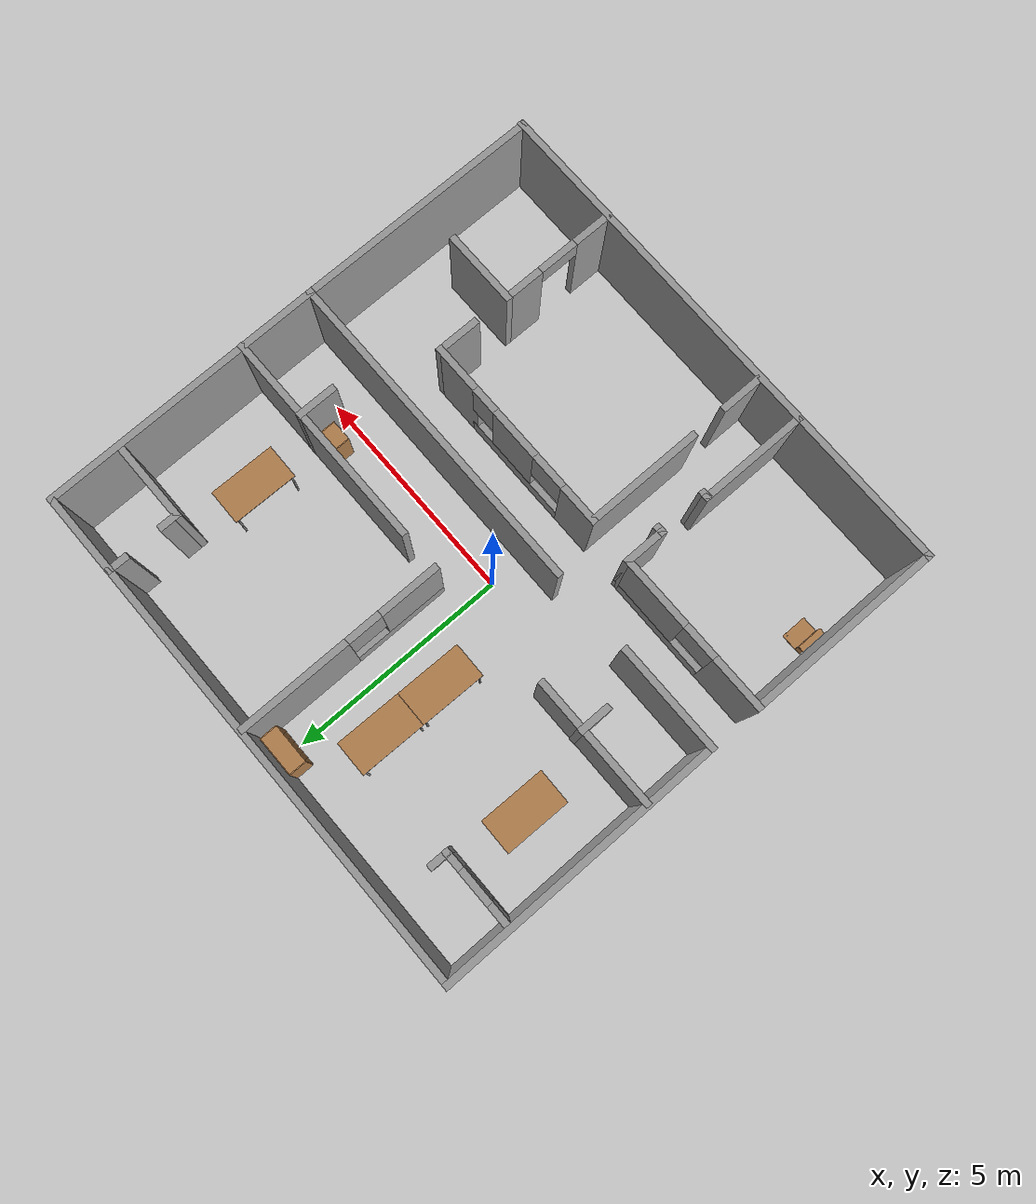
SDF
<sdf version="1.6">
 <world name="default">
  <light name="sun" type="directional">
   <pose>0 0 10 0 -0 0</pose>
   <diffuse>0.8 0.8 0.8 1</diffuse>
   <specular>0.2 0.2 0.2 1</specular>
   <attenuation>
    <range>1000</range>
    <constant>0.9</constant>
    <linear>0.01</linear>
    <quadratic>0.001</quadratic>
   </attenuation>
   <direction>-0.5 0.1 -0.9</direction>
  </light>
  <model name="ground_plane">
   <static>1</static>
   <link name="link">
    <collision name="collision">
     <geometry><plane><normal>0 0 1</normal><size>100 100</size></plane></geometry>
     <surface><friction><ode><mu>100</mu><mu2>50</mu2></ode></friction></surface>
    </collision>
    <visual name="visual">
     <cast_shadows>0</cast_shadows>
     <geometry><plane><normal>0 0 1</normal><size>100 100</size></plane></geometry>
     <material>
      <script><uri>file://media/materials/scripts/gazebo.material</uri><name>Gazebo/Grey</name></script>
     </material>
    </visual>
   </link>
  </model>
  <gravity>0 0 -9.8</gravity>
  <magnetic_field>6e-06 2.3e-05 -4.2e-05</magnetic_field>
  <atmosphere type="adiabatic"/>
  <physics name="default_physics" default="0" type="ode">
   <max_step_size>0.001</max_step_size>
   <real_time_factor>1</real_time_factor>
   <real_time_update_rate>1000</real_time_update_rate>
  </physics>
  <scene><ambient>0.4 0.4 0.4 1</ambient><background>0.7 0.7 0.7 1</background><shadows>1</shadows></scene>
  <audio><device>default</device></audio>
  <spherical_coordinates>
   <surface_model>EARTH_WGS84</surface_model>
   <latitude_deg>0</latitude_deg>
   <longitude_deg>0</longitude_deg>
   <elevation>0</elevation>
   <heading_deg>0</heading_deg>
  </spherical_coordinates>
  <model name="office01">
   <pose>0.568925 2.3845 0 0 -0 0</pose>
   <link name="Wall_0">
    <collision name="Wall_0_Collision">
     <geometry><box><size>6.50002 0.15 2.5</size></box></geometry>
     <pose>0 0 1.25 0 -0 0</pose>
    </collision>
    <visual name="Wall_0_Visual">
     <pose>0 0 1.25 0 -0 0</pose>
     <geometry><box><size>6.50002 0.15 2.5</size></box></geometry>
     <material>
      <script><uri>file://media/materials/scripts/gazebo.material</uri><name>Gazebo/Grey</name></script>
      <ambient>1 1 1 1</ambient>
     </material>
     <meta><layer>0</layer></meta>
    </visual>
    <pose>-5.80875 0 0 0 -0 -1.56809</pose>
   </link>
   <link name="Wall_10">
    <collision name="Wall_10_Collision">
     <geometry><box><size>3 0.15 2.5</size></box></geometry>
     <pose>0 0 1.25 0 -0 0</pose>
    </collision>
    <visual name="Wall_10_Visual">
     <pose>0 0 1.25 0 -0 0</pose>
     <geometry><box><size>3 0.15 2.5</size></box></geometry>
     <material>
      <script><uri>file://media/materials/scripts/gazebo.material</uri><name>Gazebo/Grey</name></script>
      <ambient>1 1 1 1</ambient>
     </material>
     <meta><layer>0</layer></meta>
    </visual>
    <pose>-4.33368 -1.60273 0 0 -0 0</pose>
   </link>
   <link name="Wall_2">
    <collision name="Wall_2_Collision">
     <geometry><box><size>6.5 0.15 2.5</size></box></geometry>
     <pose>0 0 1.25 0 -0 0</pose>
    </collision>
    <visual name="Wall_2_Visual">
     <pose>0 0 1.25 0 -0 0</pose>
     <geometry><box><size>6.5 0.15 2.5</size></box></geometry>
     <material>
      <script><uri>file://media/materials/scripts/gazebo.material</uri><name>Gazebo/Grey</name></script>
      <ambient>1 1 1 1</ambient>
     </material>
     <meta><layer>0</layer></meta>
    </visual>
    <pose>5.79985 0 0 0 -0 1.57621</pose>
   </link>
   <link name="Wall_20">
    <collision name="Wall_20_Collision">
     <geometry><box><size>1.942 0.15 2.5</size></box></geometry>
     <pose>0 0 1.25 0 -0 0</pose>
    </collision>
    <visual name="Wall_20_Visual">
     <pose>0 0 1.25 0 -0 0</pose>
     <geometry><box><size>1.942 0.15 2.5</size></box></geometry>
     <material>
      <script><uri>file://media/materials/scripts/gazebo.material</uri><name>Gazebo/Grey</name></script>
      <ambient>1 1 1 1</ambient>
     </material>
     <meta><layer>0</layer></meta>
    </visual>
    <pose>4.89205 1.56449 0 0 -0 0</pose>
   </link>
   <link name="Wall_29">
    <pose>-4.87284 1.70799 0 0 -0 3.14159</pose>
    <visual name="Wall_29_Visual_0">
     <pose>-0.643503 0 1.25 0 -0 0</pose>
     <geometry><box><size>0.462994 0.15 2.5</size></box></geometry>
     <material>
      <script><uri>file://media/materials/scripts/gazebo.material</uri><name>Gazebo/Grey</name></script>
      <ambient>1 1 1 1</ambient>
     </material>
     <meta><layer>0</layer></meta>
    </visual>
    <collision name="Wall_29_Collision_0">
     <geometry><box><size>0.462994 0.15 2.5</size></box></geometry>
     <pose>-0.643503 0 1.25 0 -0 0</pose>
    </collision>
    <visual name="Wall_29_Visual_1">
     <pose>0.231497 0 0.25 0 -0 0</pose>
     <geometry><box><size>1.28701 0.15 0.5</size></box></geometry>
     <material>
      <script><uri>file://media/materials/scripts/gazebo.material</uri><name>Gazebo/Grey</name></script>
      <ambient>1 1 1 1</ambient>
     </material>
     <meta><layer>0</layer></meta>
    </visual>
    <collision name="Wall_29_Collision_1">
     <geometry><box><size>1.28701 0.15 0.5</size></box></geometry>
     <pose>0.231497 0 0.25 0 -0 0</pose>
    </collision>
    <visual name="Wall_29_Visual_2">
     <pose>0.631497 0 1.5 0 -0 0</pose>
     <geometry><box><size>0.487006 0.15 2</size></box></geometry>
     <material>
      <script><uri>file://media/materials/scripts/gazebo.material</uri><name>Gazebo/Grey</name></script>
      <ambient>1 1 1 1</ambient>
     </material>
     <meta><layer>0</layer></meta>
    </visual>
    <collision name="Wall_29_Collision_2">
     <geometry><box><size>0.487006 0.15 2</size></box></geometry>
     <pose>0.631497 0 1.5 0 -0 0</pose>
    </collision>
    <visual name="Wall_29_Visual_3">
     <pose>-0.012006 0 1.9 0 -0 0</pose>
     <geometry><box><size>0.8 0.15 1.2</size></box></geometry>
     <material>
      <script><uri>file://media/materials/scripts/gazebo.material</uri><name>Gazebo/Grey</name></script>
      <ambient>1 1 1 1</ambient>
     </material>
     <meta><layer>0</layer></meta>
    </visual>
    <collision name="Wall_29_Collision_3">
     <geometry><box><size>0.8 0.15 1.2</size></box></geometry>
     <pose>-0.012006 0 1.9 0 -0 0</pose>
    </collision>
   </link>
   <link name="Wall_31">
    <collision name="Wall_31_Collision">
     <geometry><box><size>0.5 0.15 2.5</size></box></geometry>
     <pose>0 0 1.25 0 -0 0</pose>
    </collision>
    <visual name="Wall_31_Visual">
     <pose>0 0 1.25 0 -0 0</pose>
     <geometry><box><size>0.5 0.15 2.5</size></box></geometry>
     <material>
      <script><uri>file://media/materials/scripts/gazebo.material</uri><name>Gazebo/Grey</name></script>
      <ambient>1 1 1 1</ambient>
     </material>
     <meta><layer>0</layer></meta>
    </visual>
    <pose>-4.07284 1.88298 0 0 -0 1.5708</pose>
   </link>
   <link name="Wall_33">
    <collision name="Wall_33_Collision">
     <geometry><box><size>0.75 0.15 2.5</size></box></geometry>
     <pose>0 0 1.25 0 -0 0</pose>
    </collision>
    <visual name="Wall_33_Visual">
     <pose>0 0 1.25 0 -0 0</pose>
     <geometry><box><size>0.75 0.15 2.5</size></box></geometry>
     <material>
      <script><uri>file://media/materials/scripts/gazebo.material</uri><name>Gazebo/Grey</name></script>
      <ambient>1 1 1 1</ambient>
     </material>
     <meta><layer>0</layer></meta>
    </visual>
    <pose>-4.01825 -1.89025 0 0 -0 -1.5708</pose>
   </link>
   <link name="Wall_36">
    <collision name="Wall_36_Collision">
     <geometry><box><size>2.5 0.15 2.5</size></box></geometry>
     <pose>0 0 1.25 0 -0 0</pose>
    </collision>
    <visual name="Wall_36_Visual">
     <pose>0 0 1.25 0 -0 0</pose>
     <geometry><box><size>2.5 0.15 2.5</size></box></geometry>
     <material>
      <script><uri>file://media/materials/scripts/gazebo.material</uri><name>Gazebo/Grey</name></script>
      <ambient>1 1 1 1</ambient>
     </material>
     <meta><layer>0</layer></meta>
    </visual>
    <pose>-4.62515 -3.175 0 0 -0 0</pose>
   </link>
   <link name="Wall_38">
    <collision name="Wall_38_Collision">
     <geometry><box><size>7.5 0.15 2.5</size></box></geometry>
     <pose>0 0 1.25 0 -0 0</pose>
    </collision>
    <visual name="Wall_38_Visual">
     <pose>0 0 1.25 0 -0 0</pose>
     <geometry><box><size>7.5 0.15 2.5</size></box></geometry>
     <material>
      <script><uri>file://media/materials/scripts/gazebo.material</uri><name>Gazebo/Grey</name></script>
      <ambient>1 1 1 1</ambient>
     </material>
     <meta><layer>0</layer></meta>
    </visual>
    <pose>2.14205 -3.175 0 0 -0 3.14159</pose>
   </link>
   <link name="Wall_4">
    <collision name="Wall_4_Collision">
     <geometry><box><size>11.75 0.15 2.5</size></box></geometry>
     <pose>0 0 1.25 0 -0 0</pose>
    </collision>
    <visual name="Wall_4_Visual">
     <pose>0 0 1.25 0 -0 0</pose>
     <geometry><box><size>11.75 0.15 2.5</size></box></geometry>
     <material>
      <script><uri>file://media/materials/scripts/gazebo.material</uri><name>Gazebo/Grey</name></script>
      <ambient>1 1 1 1</ambient>
     </material>
     <meta><layer>0</layer></meta>
    </visual>
    <pose>-0.017345 3.175 0 0 -0 0</pose>
   </link>
   <link name="Wall_40">
    <collision name="Wall_40_Collision">
     <geometry><box><size>0.927 0.15 2.5</size></box></geometry>
     <pose>0 0 1.25 0 -0 0</pose>
    </collision>
    <visual name="Wall_40_Visual">
     <pose>0 0 1.25 0 -0 0</pose>
     <geometry><box><size>0.927 0.15 2.5</size></box></geometry>
     <material>
      <script><uri>file://media/materials/scripts/gazebo.material</uri><name>Gazebo/Grey</name></script>
      <ambient>1 1 1 1</ambient>
     </material>
     <meta><layer>0</layer></meta>
    </visual>
    <pose>4.01205 -1.85401 0 0 -0 -1.5708</pose>
   </link>
   <link name="Wall_42">
    <collision name="Wall_42_Collision">
     <geometry><box><size>5 0.15 2.5</size></box></geometry>
     <pose>0 0 1.25 0 -0 0</pose>
    </collision>
    <visual name="Wall_42_Visual">
     <pose>0 0 1.25 0 -0 0</pose>
     <geometry><box><size>5 0.15 2.5</size></box></geometry>
     <material>
      <script><uri>file://media/materials/scripts/gazebo.material</uri><name>Gazebo/Grey</name></script>
      <ambient>1 1 1 1</ambient>
     </material>
     <meta><layer>0</layer></meta>
    </visual>
    <pose>3.39255 -1.46989 0 0 -0 3.14159</pose>
   </link>
   <link name="Wall_44">
    <pose>0.039873 0.821301 0 0 -0 -1.5708</pose>
    <visual name="Wall_44_Visual_0">
     <pose>-1.10168 0 1.25 0 -0 0</pose>
     <geometry><box><size>2.54664 0.15 2.5</size></box></geometry>
     <material>
      <script><uri>file://media/materials/scripts/gazebo.material</uri><name>Gazebo/Grey</name></script>
      <ambient>1 1 1 1</ambient>
     </material>
     <meta><layer>0</layer></meta>
    </visual>
    <collision name="Wall_44_Collision_0">
     <geometry><box><size>2.54664 0.15 2.5</size></box></geometry>
     <pose>-1.10168 0 1.25 0 -0 0</pose>
    </collision>
    <visual name="Wall_44_Visual_1">
     <pose>1.27332 0 0.25 0 -0 0</pose>
     <geometry><box><size>2.20336 0.15 0.5</size></box></geometry>
     <material>
      <script><uri>file://media/materials/scripts/gazebo.material</uri><name>Gazebo/Grey</name></script>
      <ambient>1 1 1 1</ambient>
     </material>
     <meta><layer>0</layer></meta>
    </visual>
    <collision name="Wall_44_Collision_1">
     <geometry><box><size>2.20336 0.15 0.5</size></box></geometry>
     <pose>1.27332 0 0.25 0 -0 0</pose>
    </collision>
    <visual name="Wall_44_Visual_2">
     <pose>1.67332 0 1.5 0 -0 0</pose>
     <geometry><box><size>1.40336 0.15 2</size></box></geometry>
     <material>
      <script><uri>file://media/materials/scripts/gazebo.material</uri><name>Gazebo/Grey</name></script>
      <ambient>1 1 1 1</ambient>
     </material>
     <meta><layer>0</layer></meta>
    </visual>
    <collision name="Wall_44_Collision_2">
     <geometry><box><size>1.40336 0.15 2</size></box></geometry>
     <pose>1.67332 0 1.5 0 -0 0</pose>
    </collision>
    <visual name="Wall_44_Visual_3">
     <pose>0.571641 0 1.9 0 -0 0</pose>
     <geometry><box><size>0.8 0.15 1.2</size></box></geometry>
     <material>
      <script><uri>file://media/materials/scripts/gazebo.material</uri><name>Gazebo/Grey</name></script>
      <ambient>1 1 1 1</ambient>
     </material>
     <meta><layer>0</layer></meta>
    </visual>
    <collision name="Wall_44_Collision_3">
     <geometry><box><size>0.8 0.15 1.2</size></box></geometry>
     <pose>0.571641 0 1.9 0 -0 0</pose>
    </collision>
   </link>
   <link name="Wall_46">
    <collision name="Wall_46_Collision">
     <geometry><box><size>0.5 0.15 2.5</size></box></geometry>
     <pose>0 0 1.25 0 -0 0</pose>
    </collision>
    <visual name="Wall_46_Visual">
     <pose>0 0 1.25 0 -0 0</pose>
     <geometry><box><size>0.5 0.15 2.5</size></box></geometry>
     <material>
      <script><uri>file://media/materials/scripts/gazebo.material</uri><name>Gazebo/Grey</name></script>
      <ambient>1 1 1 1</ambient>
     </material>
     <meta><layer>0</layer></meta>
    </visual>
    <pose>3.97763 2.98069 0 0 -0 -1.5708</pose>
   </link>
   <link name="Wall_48">
    <collision name="Wall_48_Collision">
     <geometry><box><size>0.5 0.15 2.5</size></box></geometry>
     <pose>0 0 1.25 0 -0 0</pose>
    </collision>
    <visual name="Wall_48_Visual">
     <pose>0 0 1.25 0 -0 0</pose>
     <geometry><box><size>0.5 0.15 2.5</size></box></geometry>
     <material>
      <script><uri>file://media/materials/scripts/gazebo.material</uri><name>Gazebo/Grey</name></script>
      <ambient>1 1 1 1</ambient>
     </material>
     <meta><layer>0</layer></meta>
    </visual>
    <pose>3.99605 1.73949 0 0 -0 1.5708</pose>
   </link>
   <link name="Wall_7">
    <collision name="Wall_7_Collision">
     <geometry><box><size>0.15 0.15 2.5</size></box></geometry>
     <pose>0 0 1.25 0 -0 0</pose>
    </collision>
    <visual name="Wall_7_Visual">
     <pose>0 0 1.25 0 -0 0</pose>
     <geometry><box><size>0.15 0.15 2.5</size></box></geometry>
     <material>
      <script><uri>file://media/materials/scripts/gazebo.material</uri><name>Gazebo/Grey</name></script>
      <ambient>1 1 1 1</ambient>
     </material>
     <meta><layer>0</layer></meta>
    </visual>
    <pose>-4.07284 1.70799 0 0 -0 0</pose>
   </link>
   <static>1</static>
  </model>
  <model name="table">
   <static>1</static>
   <link name="link">
    <collision name="surface">
     <pose>0 0 1 0 -0 0</pose>
     <geometry><box><size>1.5 0.8 0.03</size></box></geometry>
     <surface><friction><ode><mu>0.6</mu><mu2>0.6</mu2></ode></friction></surface>
    </collision>
    <visual name="visual1">
     <pose>0 0 1 0 -0 0</pose>
     <geometry><box><size>1.5 0.8 0.03</size></box></geometry>
     <material>
      <script><uri>file://media/materials/scripts/gazebo.material</uri><name>Gazebo/Wood</name></script>
     </material>
    </visual>
    <collision name="front_left_leg">
     <pose>0.68 0.38 0.5 0 -0 0</pose>
     <geometry><cylinder><radius>0.02</radius><length>1</length></cylinder></geometry>
    </collision>
    <visual name="front_left_leg">
     <pose>0.68 0.38 0.5 0 -0 0</pose>
     <geometry><cylinder><radius>0.02</radius><length>1</length></cylinder></geometry>
     <material>
      <script><uri>file://media/materials/scripts/gazebo.material</uri><name>Gazebo/Grey</name></script>
     </material>
    </visual>
    <collision name="front_right_leg">
     <pose>0.68 -0.38 0.5 0 -0 0</pose>
     <geometry><cylinder><radius>0.02</radius><length>1</length></cylinder></geometry>
    </collision>
    <visual name="front_right_leg">
     <pose>0.68 -0.38 0.5 0 -0 0</pose>
     <geometry><cylinder><radius>0.02</radius><length>1</length></cylinder></geometry>
     <material>
      <script><uri>file://media/materials/scripts/gazebo.material</uri><name>Gazebo/Grey</name></script>
     </material>
    </visual>
    <collision name="back_right_leg">
     <pose>-0.68 -0.38 0.5 0 -0 0</pose>
     <geometry><cylinder><radius>0.02</radius><length>1</length></cylinder></geometry>
    </collision>
    <visual name="back_right_leg">
     <pose>-0.68 -0.38 0.5 0 -0 0</pose>
     <geometry><cylinder><radius>0.02</radius><length>1</length></cylinder></geometry>
     <material>
      <script><uri>file://media/materials/scripts/gazebo.material</uri><name>Gazebo/Grey</name></script>
     </material>
    </visual>
    <collision name="back_left_leg">
     <pose>-0.68 0.38 0.5 0 -0 0</pose>
     <geometry><cylinder><radius>0.02</radius><length>1</length></cylinder></geometry>
    </collision>
    <visual name="back_left_leg">
     <pose>-0.68 0.38 0.5 0 -0 0</pose>
     <geometry><cylinder><radius>0.02</radius><length>1</length></cylinder></geometry>
     <material>
      <script><uri>file://media/materials/scripts/gazebo.material</uri><name>Gazebo/Grey</name></script>
     </material>
    </visual>
   </link>
   <pose>-3.88185 2.51317 0 0 -0 1.5589</pose>
  </model>
  <model name="table_clone">
   <static>1</static>
   <link name="link">
    <collision name="surface">
     <pose>0 0 1 0 -0 0</pose>
     <geometry><box><size>1.5 0.8 0.03</size></box></geometry>
     <surface><friction><ode><mu>0.6</mu><mu2>0.6</mu2></ode></friction></surface>
    </collision>
    <visual name="visual1">
     <pose>0 0 1 0 -0 0</pose>
     <geometry><box><size>1.5 0.8 0.03</size></box></geometry>
     <material>
      <script><uri>file://media/materials/scripts/gazebo.material</uri><name>Gazebo/Wood</name></script>
     </material>
    </visual>
    <collision name="front_left_leg">
     <pose>0.68 0.38 0.5 0 -0 0</pose>
     <geometry><cylinder><radius>0.02</radius><length>1</length></cylinder></geometry>
    </collision>
    <visual name="front_left_leg">
     <pose>0.68 0.38 0.5 0 -0 0</pose>
     <geometry><cylinder><radius>0.02</radius><length>1</length></cylinder></geometry>
     <material>
      <script><uri>file://media/materials/scripts/gazebo.material</uri><name>Gazebo/Grey</name></script>
     </material>
    </visual>
    <collision name="front_right_leg">
     <pose>0.68 -0.38 0.5 0 -0 0</pose>
     <geometry><cylinder><radius>0.02</radius><length>1</length></cylinder></geometry>
    </collision>
    <visual name="front_right_leg">
     <pose>0.68 -0.38 0.5 0 -0 0</pose>
     <geometry><cylinder><radius>0.02</radius><length>1</length></cylinder></geometry>
     <material>
      <script><uri>file://media/materials/scripts/gazebo.material</uri><name>Gazebo/Grey</name></script>
     </material>
    </visual>
    <collision name="back_right_leg">
     <pose>-0.68 -0.38 0.5 0 -0 0</pose>
     <geometry><cylinder><radius>0.02</radius><length>1</length></cylinder></geometry>
    </collision>
    <visual name="back_right_leg">
     <pose>-0.68 -0.38 0.5 0 -0 0</pose>
     <geometry><cylinder><radius>0.02</radius><length>1</length></cylinder></geometry>
     <material>
      <script><uri>file://media/materials/scripts/gazebo.material</uri><name>Gazebo/Grey</name></script>
     </material>
    </visual>
    <collision name="back_left_leg">
     <pose>-0.68 0.38 0.5 0 -0 0</pose>
     <geometry><cylinder><radius>0.02</radius><length>1</length></cylinder></geometry>
    </collision>
    <visual name="back_left_leg">
     <pose>-0.68 0.38 0.5 0 -0 0</pose>
     <geometry><cylinder><radius>0.02</radius><length>1</length></cylinder></geometry>
     <material>
      <script><uri>file://media/materials/scripts/gazebo.material</uri><name>Gazebo/Grey</name></script>
     </material>
    </visual>
   </link>
   <pose>-0.955712 3.66797 0 0 -0 1.5589</pose>
  </model>
  <model name="table_clone_0">
   <static>1</static>
   <link name="link">
    <collision name="surface">
     <pose>0 0 1 0 -0 0</pose>
     <geometry><box><size>1.5 0.8 0.03</size></box></geometry>
     <surface><friction><ode><mu>0.6</mu><mu2>0.6</mu2></ode></friction></surface>
    </collision>
    <visual name="visual1">
     <pose>0 0 1 0 -0 0</pose>
     <geometry><box><size>1.5 0.8 0.03</size></box></geometry>
     <material>
      <script><uri>file://media/materials/scripts/gazebo.material</uri><name>Gazebo/Wood</name></script>
     </material>
    </visual>
    <collision name="front_left_leg">
     <pose>0.68 0.38 0.5 0 -0 0</pose>
     <geometry><cylinder><radius>0.02</radius><length>1</length></cylinder></geometry>
    </collision>
    <visual name="front_left_leg">
     <pose>0.68 0.38 0.5 0 -0 0</pose>
     <geometry><cylinder><radius>0.02</radius><length>1</length></cylinder></geometry>
     <material>
      <script><uri>file://media/materials/scripts/gazebo.material</uri><name>Gazebo/Grey</name></script>
     </material>
    </visual>
    <collision name="front_right_leg">
     <pose>0.68 -0.38 0.5 0 -0 0</pose>
     <geometry><cylinder><radius>0.02</radius><length>1</length></cylinder></geometry>
    </collision>
    <visual name="front_right_leg">
     <pose>0.68 -0.38 0.5 0 -0 0</pose>
     <geometry><cylinder><radius>0.02</radius><length>1</length></cylinder></geometry>
     <material>
      <script><uri>file://media/materials/scripts/gazebo.material</uri><name>Gazebo/Grey</name></script>
     </material>
    </visual>
    <collision name="back_right_leg">
     <pose>-0.68 -0.38 0.5 0 -0 0</pose>
     <geometry><cylinder><radius>0.02</radius><length>1</length></cylinder></geometry>
    </collision>
    <visual name="back_right_leg">
     <pose>-0.68 -0.38 0.5 0 -0 0</pose>
     <geometry><cylinder><radius>0.02</radius><length>1</length></cylinder></geometry>
     <material>
      <script><uri>file://media/materials/scripts/gazebo.material</uri><name>Gazebo/Grey</name></script>
     </material>
    </visual>
    <collision name="back_left_leg">
     <pose>-0.68 0.38 0.5 0 -0 0</pose>
     <geometry><cylinder><radius>0.02</radius><length>1</length></cylinder></geometry>
    </collision>
    <visual name="back_left_leg">
     <pose>-0.68 0.38 0.5 0 -0 0</pose>
     <geometry><cylinder><radius>0.02</radius><length>1</length></cylinder></geometry>
     <material>
      <script><uri>file://media/materials/scripts/gazebo.material</uri><name>Gazebo/Grey</name></script>
     </material>
    </visual>
   </link>
   <pose>-0.975228 2.16546 0 0 -0 1.5589</pose>
  </model>
  <model name="table_clone_1">
   <static>1</static>
   <link name="link">
    <collision name="surface">
     <pose>0 0 1 0 -0 0</pose>
     <geometry><box><size>1.5 0.8 0.03</size></box></geometry>
     <surface><friction><ode><mu>0.6</mu><mu2>0.6</mu2></ode></friction></surface>
    </collision>
    <visual name="visual1">
     <pose>0 0 1 0 -0 0</pose>
     <geometry><box><size>1.5 0.8 0.03</size></box></geometry>
     <material>
      <script><uri>file://media/materials/scripts/gazebo.material</uri><name>Gazebo/Wood</name></script>
     </material>
    </visual>
    <collision name="front_left_leg">
     <pose>0.68 0.38 0.5 0 -0 0</pose>
     <geometry><cylinder><radius>0.02</radius><length>1</length></cylinder></geometry>
    </collision>
    <visual name="front_left_leg">
     <pose>0.68 0.38 0.5 0 -0 0</pose>
     <geometry><cylinder><radius>0.02</radius><length>1</length></cylinder></geometry>
     <material>
      <script><uri>file://media/materials/scripts/gazebo.material</uri><name>Gazebo/Grey</name></script>
     </material>
    </visual>
    <collision name="front_right_leg">
     <pose>0.68 -0.38 0.5 0 -0 0</pose>
     <geometry><cylinder><radius>0.02</radius><length>1</length></cylinder></geometry>
    </collision>
    <visual name="front_right_leg">
     <pose>0.68 -0.38 0.5 0 -0 0</pose>
     <geometry><cylinder><radius>0.02</radius><length>1</length></cylinder></geometry>
     <material>
      <script><uri>file://media/materials/scripts/gazebo.material</uri><name>Gazebo/Grey</name></script>
     </material>
    </visual>
    <collision name="back_right_leg">
     <pose>-0.68 -0.38 0.5 0 -0 0</pose>
     <geometry><cylinder><radius>0.02</radius><length>1</length></cylinder></geometry>
    </collision>
    <visual name="back_right_leg">
     <pose>-0.68 -0.38 0.5 0 -0 0</pose>
     <geometry><cylinder><radius>0.02</radius><length>1</length></cylinder></geometry>
     <material>
      <script><uri>file://media/materials/scripts/gazebo.material</uri><name>Gazebo/Grey</name></script>
     </material>
    </visual>
    <collision name="back_left_leg">
     <pose>-0.68 0.38 0.5 0 -0 0</pose>
     <geometry><cylinder><radius>0.02</radius><length>1</length></cylinder></geometry>
    </collision>
    <visual name="back_left_leg">
     <pose>-0.68 0.38 0.5 0 -0 0</pose>
     <geometry><cylinder><radius>0.02</radius><length>1</length></cylinder></geometry>
     <material>
      <script><uri>file://media/materials/scripts/gazebo.material</uri><name>Gazebo/Grey</name></script>
     </material>
    </visual>
   </link>
   <pose>4.539 2.42439 0 0 -0 1.5589</pose>
  </model>
  <model name="bookshelf">
   <static>1</static>
   <link name="link">
    <inertial><mass>1</mass></inertial>
    <collision name="back">
     <pose>0 0.005 0.6 0 -0 0</pose>
     <geometry><box><size>0.9 0.01 1.2</size></box></geometry>
    </collision>
    <visual name="visual1">
     <pose>0 0.005 0.6 0 -0 0</pose>
     <geometry><box><size>0.9 0.01 1.2</size></box></geometry>
     <material>
      <script><uri>file://media/materials/scripts/gazebo.material</uri><name>Gazebo/Wood</name></script>
     </material>
    </visual>
    <collision name="left_side">
     <pose>0.45 -0.195 0.6 0 -0 0</pose>
     <geometry><box><size>0.02 0.4 1.2</size></box></geometry>
    </collision>
    <visual name="visual2">
     <pose>0.45 -0.195 0.6 0 -0 0</pose>
     <geometry><box><size>0.02 0.4 1.2</size></box></geometry>
     <material>
      <script><uri>file://media/materials/scripts/gazebo.material</uri><name>Gazebo/Wood</name></script>
     </material>
    </visual>
    <collision name="right_side">
     <pose>-0.45 -0.195 0.6 0 -0 0</pose>
     <geometry><box><size>0.02 0.4 1.2</size></box></geometry>
    </collision>
    <visual name="visual3">
     <pose>-0.45 -0.195 0.6 0 -0 0</pose>
     <geometry><box><size>0.02 0.4 1.2</size></box></geometry>
     <material>
      <script><uri>file://media/materials/scripts/gazebo.material</uri><name>Gazebo/Wood</name></script>
     </material>
    </visual>
    <collision name="bottom">
     <pose>0 -0.195 0.03 0 -0 0</pose>
     <geometry><box><size>0.88 0.4 0.06</size></box></geometry>
    </collision>
    <visual name="visual4">
     <pose>0 -0.195 0.03 0 -0 0</pose>
     <geometry><box><size>0.88 0.4 0.06</size></box></geometry>
     <material>
      <script><uri>file://media/materials/scripts/gazebo.material</uri><name>Gazebo/Wood</name></script>
     </material>
    </visual>
    <collision name="top">
     <pose>0 -0.195 1.19 0 -0 0</pose>
     <geometry><box><size>0.88 0.4 0.02</size></box></geometry>
    </collision>
    <visual name="visual5">
     <pose>0 -0.195 1.19 0 -0 0</pose>
     <geometry><box><size>0.88 0.4 0.02</size></box></geometry>
     <material>
      <script><uri>file://media/materials/scripts/gazebo.material</uri><name>Gazebo/Wood</name></script>
     </material>
    </visual>
    <collision name="low_shelf">
     <pose>0 -0.195 0.43 0 -0 0</pose>
     <geometry><box><size>0.88 0.4 0.02</size></box></geometry>
    </collision>
    <visual name="visual6">
     <pose>0 -0.195 0.43 0 -0 0</pose>
     <geometry><box><size>0.88 0.4 0.02</size></box></geometry>
     <material>
      <script><uri>file://media/materials/scripts/gazebo.material</uri><name>Gazebo/Wood</name></script>
     </material>
    </visual>
    <collision name="high_shelf">
     <pose>0 -0.195 0.8 0 -0 0</pose>
     <geometry><box><size>0.88 0.4 0.02</size></box></geometry>
    </collision>
    <visual name="visual7">
     <pose>0 -0.195 0.8 0 -0 0</pose>
     <geometry><box><size>0.88 0.4 0.02</size></box></geometry>
     <material>
      <script><uri>file://media/materials/scripts/gazebo.material</uri><name>Gazebo/Wood</name></script>
     </material>
    </visual>
   </link>
   <pose>0.010642 5.47388 0 0 -0 0</pose>
  </model>
  <model name="cabinet">
   <static>1</static>
   <link name="cabinet_bottom_plate">
    <inertial>
     <pose>0 0 -1 0 -0 0</pose>
     <inertia><ixx>2.05</ixx><ixy>0</ixy><ixz>0</ixz><iyy>2.05</iyy><iyz>0</iyz><izz>2.05</izz></inertia>
     <mass>25</mass>
    </inertial>
    <collision name="cabinet_bottom_plate_geom">
     <pose>0 0 0.01 0 -0 0</pose>
     <geometry><box><size>0.45 0.45 0.02</size></box></geometry>
    </collision>
    <visual name="cabinet_bottom_plate_geom_visual">
     <pose>0 0 0.01 0 -0 0</pose>
     <geometry><box><size>0.45 0.45 0.02</size></box></geometry>
     <material>
      <script><uri>file://media/materials/scripts/gazebo.material</uri><name>Gazebo/Wood</name></script>
     </material>
    </visual>
    <collision name="cabinet_bottom_plate_geom_cabinet_back_plate">
     <pose>0.235 0 0.51 0 -0 0</pose>
     <geometry><box><size>0.02 0.45 1.02</size></box></geometry>
    </collision>
    <visual name="cabinet_bottom_plate_geom_cabinet_back_plate_visual">
     <pose>0.235 0 0.51 0 -0 0</pose>
     <geometry><box><size>0.02 0.45 1.02</size></box></geometry>
     <material>
      <script><uri>file://media/materials/scripts/gazebo.material</uri><name>Gazebo/Wood</name></script>
     </material>
    </visual>
    <collision name="cabinet_bottom_plate_geom_cabinet_left_plate">
     <pose>0 0.235 0.51 0 -0 0</pose>
     <geometry><box><size>0.45 0.02 1.02</size></box></geometry>
    </collision>
    <visual name="cabinet_bottom_plate_geom_cabinet_left_plate_visual">
     <pose>0 0.235 0.51 0 -0 0</pose>
     <geometry><box><size>0.45 0.02 1.02</size></box></geometry>
     <material>
      <script><uri>file://media/materials/scripts/gazebo.material</uri><name>Gazebo/Wood</name></script>
     </material>
    </visual>
    <collision name="cabinet_bottom_plate_geom_cabinet_middle_plate">
     <pose>0 0 0.51 0 -0 0</pose>
     <geometry><box><size>0.45 0.45 0.02</size></box></geometry>
    </collision>
    <visual name="cabinet_bottom_plate_geom_cabinet_middle_plate_visual">
     <pose>0 0 0.51 0 -0 0</pose>
     <geometry><box><size>0.45 0.45 0.02</size></box></geometry>
     <material>
      <script><uri>file://media/materials/scripts/gazebo.material</uri><name>Gazebo/Wood</name></script>
     </material>
    </visual>
    <collision name="cabinet_bottom_plate_geom_cabinet_right_plate">
     <pose>0 -0.235 0.51 0 -0 0</pose>
     <geometry><box><size>0.45 0.02 1.02</size></box></geometry>
    </collision>
    <visual name="cabinet_bottom_plate_geom_cabinet_right_plate_visual">
     <pose>0 -0.235 0.51 0 -0 0</pose>
     <geometry><box><size>0.45 0.02 1.02</size></box></geometry>
     <material>
      <script><uri>file://media/materials/scripts/gazebo.material</uri><name>Gazebo/Wood</name></script>
     </material>
    </visual>
    <collision name="cabinet_bottom_plate_geom_cabinet_top_plate">
     <pose>0 0 1.01 0 -0 0</pose>
     <geometry><box><size>0.45 0.45 0.02</size></box></geometry>
    </collision>
    <visual name="cabinet_bottom_plate_geom_cabinet_top_plate_visual">
     <pose>0 0 1.01 0 -0 0</pose>
     <geometry><box><size>0.45 0.45 0.02</size></box></geometry>
     <material>
      <script><uri>file://media/materials/scripts/gazebo.material</uri><name>Gazebo/Wood</name></script>
     </material>
    </visual>
   </link>
   <pose>4.25998 0.58904 0 0 -0 1.57541</pose>
  </model>
  <model name="office01add">
   <pose>-4.3 -4.1 0 0 -0 0</pose>
   <link name="Wall_21">
    <collision name="Wall_21_Collision">
     <geometry><box><size>5.75 0.15 2.5</size></box></geometry>
     <pose>0 0 1.25 0 -0 0</pose>
    </collision>
    <visual name="Wall_21_Visual">
     <pose>0 0 1.25 0 -0 0</pose>
     <geometry><box><size>5.75 0.15 2.5</size></box></geometry>
     <material>
      <script><uri>file://media/materials/scripts/gazebo.material</uri><name>Gazebo/Grey</name></script>
      <ambient>1 1 1 1</ambient>
     </material>
     <meta><layer>0</layer></meta>
    </visual>
    <pose>26944.8 24305.2 0 0 -0 -1.5708</pose>
   </link>
   <link name="Wall_23">
    <collision name="Wall_23_Collision">
     <geometry><box><size>11.75 0.15 2.5</size></box></geometry>
     <pose>0 0 1.25 0 -0 0</pose>
    </collision>
    <visual name="Wall_23_Visual">
     <pose>0 0 1.25 0 -0 0</pose>
     <geometry><box><size>11.75 0.15 2.5</size></box></geometry>
     <material>
      <script><uri>file://media/materials/scripts/gazebo.material</uri><name>Gazebo/Grey</name></script>
      <ambient>1 1 1 1</ambient>
     </material>
     <meta><layer>0</layer></meta>
    </visual>
    <pose>26950.6 24302.4 0 0 -0 0</pose>
   </link>
   <link name="Wall_25">
    <collision name="Wall_25_Collision">
     <geometry><box><size>5.75 0.15 2.5</size></box></geometry>
     <pose>0 0 1.25 0 -0 0</pose>
    </collision>
    <visual name="Wall_25_Visual">
     <pose>0 0 1.25 0 -0 0</pose>
     <geometry><box><size>5.75 0.15 2.5</size></box></geometry>
     <material>
      <script><uri>file://media/materials/scripts/gazebo.material</uri><name>Gazebo/Grey</name></script>
      <ambient>1 1 1 1</ambient>
     </material>
     <meta><layer>0</layer></meta>
    </visual>
    <pose>26956.4 24305.2 0 0 -0 1.5708</pose>
   </link>
   <link name="Wall_27">
    <collision name="Wall_27_Collision">
     <geometry><box><size>3 0.15 2.5</size></box></geometry>
     <pose>0 0 1.25 0 -0 0</pose>
    </collision>
    <visual name="Wall_27_Visual">
     <pose>0 0 1.25 0 -0 0</pose>
     <geometry><box><size>3 0.15 2.5</size></box></geometry>
     <material>
      <script><uri>file://media/materials/scripts/gazebo.material</uri><name>Gazebo/Grey</name></script>
      <ambient>1 1 1 1</ambient>
     </material>
     <meta><layer>0</layer></meta>
    </visual>
    <pose>26950.6 24305.2 0 0 -0 1.5708</pose>
   </link>
   <link name="Wall_32">
    <collision name="Wall_32_Collision">
     <geometry><box><size>0.5 0.15 2.5</size></box></geometry>
     <pose>0 0 1.25 0 -0 0</pose>
    </collision>
    <visual name="Wall_32_Visual">
     <pose>0 0 1.25 0 -0 0</pose>
     <geometry><box><size>0.5 0.15 2.5</size></box></geometry>
     <material>
      <script><uri>file://media/materials/scripts/gazebo.material</uri><name>Gazebo/Grey</name></script>
      <ambient>1 1 1 1</ambient>
     </material>
     <meta><layer>0</layer></meta>
    </visual>
    <pose>26950.6 24302.6 0 0 -0 1.5708</pose>
   </link>
   <link name="Wall_34">
    <pose>26947.2 24306.5 0 0 -0 0.000686</pose>
    <visual name="Wall_34_Visual_0">
     <pose>-1.98582 0 1.25 0 -0 0</pose>
     <geometry><box><size>1.06117 0.15 2.5</size></box></geometry>
     <material>
      <script><uri>file://media/materials/scripts/gazebo.material</uri><name>Gazebo/Grey</name></script>
      <ambient>1 1 1 1</ambient>
     </material>
     <meta><layer>0</layer></meta>
    </visual>
    <collision name="Wall_34_Collision_0">
     <geometry><box><size>1.06117 0.15 2.5</size></box></geometry>
     <pose>-1.98582 0 1.25 0 -0 0</pose>
    </collision>
    <visual name="Wall_34_Visual_1">
     <pose>0.530587 0 0.25 0 -0 0</pose>
     <geometry><box><size>3.97163 0.15 0.5</size></box></geometry>
     <material>
      <script><uri>file://media/materials/scripts/gazebo.material</uri><name>Gazebo/Grey</name></script>
      <ambient>1 1 1 1</ambient>
     </material>
     <meta><layer>0</layer></meta>
    </visual>
    <collision name="Wall_34_Collision_1">
     <geometry><box><size>3.97163 0.15 0.5</size></box></geometry>
     <pose>0.530587 0 0.25 0 -0 0</pose>
    </collision>
    <visual name="Wall_34_Visual_2">
     <pose>0.930587 0 1.5 0 -0 0</pose>
     <geometry><box><size>3.17163 0.15 2</size></box></geometry>
     <material>
      <script><uri>file://media/materials/scripts/gazebo.material</uri><name>Gazebo/Grey</name></script>
      <ambient>1 1 1 1</ambient>
     </material>
     <meta><layer>0</layer></meta>
    </visual>
    <collision name="Wall_34_Collision_2">
     <geometry><box><size>3.17163 0.15 2</size></box></geometry>
     <pose>0.930587 0 1.5 0 -0 0</pose>
    </collision>
    <visual name="Wall_34_Visual_3">
     <pose>-1.05523 0 1.9 0 -0 0</pose>
     <geometry><box><size>0.8 0.15 1.2</size></box></geometry>
     <material>
      <script><uri>file://media/materials/scripts/gazebo.material</uri><name>Gazebo/Grey</name></script>
      <ambient>1 1 1 1</ambient>
     </material>
     <meta><layer>0</layer></meta>
    </visual>
    <collision name="Wall_34_Collision_3">
     <geometry><box><size>0.8 0.15 1.2</size></box></geometry>
     <pose>-1.05523 0 1.9 0 -0 0</pose>
    </collision>
   </link>
   <link name="Wall_36">
    <collision name="Wall_36_Collision">
     <geometry><box><size>0.15 0.15 2.5</size></box></geometry>
     <pose>0 0 1.25 0 -0 0</pose>
    </collision>
    <visual name="Wall_36_Visual">
     <pose>0 0 1.25 0 -0 0</pose>
     <geometry><box><size>0.15 0.15 2.5</size></box></geometry>
     <material>
      <script><uri>file://media/materials/scripts/gazebo.material</uri><name>Gazebo/Grey</name></script>
      <ambient>1 1 1 1</ambient>
     </material>
     <meta><layer>0</layer></meta>
    </visual>
    <pose>26949.5 24303.9 0 0 -0 0</pose>
   </link>
   <link name="Wall_5">
    <collision name="Wall_5_Collision">
     <geometry><box><size>14851 0.15 2.5</size></box></geometry>
     <pose>0 0 1.25 0 -0 0</pose>
    </collision>
    <visual name="Wall_5_Visual">
     <pose>0 0 1.25 0 -0 0</pose>
     <geometry><box><size>14851 0.15 2.5</size></box></geometry>
     <material>
      <script><uri>file://media/materials/scripts/gazebo.material</uri><name>Gazebo/Grey</name></script>
      <ambient>1 1 1 1</ambient>
     </material>
     <meta><layer>0</layer></meta>
    </visual>
    <pose>-20525.7 -20595.2 0 0 -0 -0.523599</pose>
   </link>
   <link name="Wall_65">
    <pose>26947.5 24305.1 0 0 -0 -1.5708</pose>
    <visual name="Wall_65_Visual_0">
     <pose>-0.900493 0 1.25 0 -0 0</pose>
     <geometry><box><size>1.19901 0.15 2.5</size></box></geometry>
     <material>
      <script><uri>file://media/materials/scripts/gazebo.material</uri><name>Gazebo/Grey</name></script>
      <ambient>1 1 1 1</ambient>
     </material>
     <meta><layer>0</layer></meta>
    </visual>
    <collision name="Wall_65_Collision_0">
     <geometry><box><size>1.19901 0.15 2.5</size></box></geometry>
     <pose>-0.900493 0 1.25 0 -0 0</pose>
    </collision>
    <visual name="Wall_65_Visual_1">
     <pose>0.599507 0 0.25 0 -0 0</pose>
     <geometry><box><size>1.80099 0.15 0.5</size></box></geometry>
     <material>
      <script><uri>file://media/materials/scripts/gazebo.material</uri><name>Gazebo/Grey</name></script>
      <ambient>1 1 1 1</ambient>
     </material>
     <meta><layer>0</layer></meta>
    </visual>
    <collision name="Wall_65_Collision_1">
     <geometry><box><size>1.80099 0.15 0.5</size></box></geometry>
     <pose>0.599507 0 0.25 0 -0 0</pose>
    </collision>
    <visual name="Wall_65_Visual_2">
     <pose>0.999507 0 1.5 0 -0 0</pose>
     <geometry><box><size>1.00099 0.15 2</size></box></geometry>
     <material>
      <script><uri>file://media/materials/scripts/gazebo.material</uri><name>Gazebo/Grey</name></script>
      <ambient>1 1 1 1</ambient>
     </material>
     <meta><layer>0</layer></meta>
    </visual>
    <collision name="Wall_65_Collision_2">
     <geometry><box><size>1.00099 0.15 2</size></box></geometry>
     <pose>0.999507 0 1.5 0 -0 0</pose>
    </collision>
    <visual name="Wall_65_Visual_3">
     <pose>0.099014 0 1.9 0 -0 0</pose>
     <geometry><box><size>0.8 0.15 1.2</size></box></geometry>
     <material>
      <script><uri>file://media/materials/scripts/gazebo.material</uri><name>Gazebo/Grey</name></script>
      <ambient>1 1 1 1</ambient>
     </material>
     <meta><layer>0</layer></meta>
    </visual>
    <collision name="Wall_65_Collision_3">
     <geometry><box><size>0.8 0.15 1.2</size></box></geometry>
     <pose>0.099014 0 1.9 0 -0 0</pose>
    </collision>
   </link>
   <link name="Wall_68">
    <collision name="Wall_68_Collision">
     <geometry><box><size>0.15 0.15 2.5</size></box></geometry>
     <pose>0 0 1.25 0 -0 0</pose>
    </collision>
    <visual name="Wall_68_Visual">
     <pose>0 0 1.25 0 -0 0</pose>
     <geometry><box><size>0.15 0.15 2.5</size></box></geometry>
     <material>
      <script><uri>file://media/materials/scripts/gazebo.material</uri><name>Gazebo/Grey</name></script>
      <ambient>1 1 1 1</ambient>
     </material>
     <meta><layer>0</layer></meta>
    </visual>
    <pose>26949.5 24303.9 0 0 -0 0</pose>
   </link>
   <link name="Wall_72">
    <collision name="Wall_72_Collision">
     <geometry><box><size>0.5 0.15 2.5</size></box></geometry>
     <pose>0 0 1.25 0 -0 0</pose>
    </collision>
    <visual name="Wall_72_Visual">
     <pose>0 0 1.25 0 -0 0</pose>
     <geometry><box><size>0.5 0.15 2.5</size></box></geometry>
     <material>
      <script><uri>file://media/materials/scripts/gazebo.material</uri><name>Gazebo/Grey</name></script>
      <ambient>1 1 1 1</ambient>
     </material>
     <meta><layer>0</layer></meta>
    </visual>
    <pose>26947.5 24302.6 0 0 -0 1.5708</pose>
   </link>
   <link name="Wall_74">
    <collision name="Wall_74_Collision">
     <geometry><box><size>0.5 0.15 2.5</size></box></geometry>
     <pose>0 0 1.25 0 -0 0</pose>
    </collision>
    <visual name="Wall_74_Visual">
     <pose>0 0 1.25 0 -0 0</pose>
     <geometry><box><size>0.5 0.15 2.5</size></box></geometry>
     <material>
      <script><uri>file://media/materials/scripts/gazebo.material</uri><name>Gazebo/Grey</name></script>
      <ambient>1 1 1 1</ambient>
     </material>
     <meta><layer>0</layer></meta>
    </visual>
    <pose>26949.7 24302.6 0 0 -0 1.5708</pose>
   </link>
   <link name="Wall_76">
    <pose>26952.1 24306.6 0 0 -0 0</pose>
    <visual name="Wall_76_Visual_0">
     <pose>-0.925943 0 1.25 0 -0 0</pose>
     <geometry><box><size>1.14811 0.15 2.5</size></box></geometry>
     <material>
      <script><uri>file://media/materials/scripts/gazebo.material</uri><name>Gazebo/Grey</name></script>
      <ambient>1 1 1 1</ambient>
     </material>
     <meta><layer>0</layer></meta>
    </visual>
    <collision name="Wall_76_Collision_0">
     <geometry><box><size>1.14811 0.15 2.5</size></box></geometry>
     <pose>-0.925943 0 1.25 0 -0 0</pose>
    </collision>
    <visual name="Wall_76_Visual_1">
     <pose>0.574057 0 0.25 0 -0 0</pose>
     <geometry><box><size>1.85189 0.15 0.5</size></box></geometry>
     <material>
      <script><uri>file://media/materials/scripts/gazebo.material</uri><name>Gazebo/Grey</name></script>
      <ambient>1 1 1 1</ambient>
     </material>
     <meta><layer>0</layer></meta>
    </visual>
    <collision name="Wall_76_Collision_1">
     <geometry><box><size>1.85189 0.15 0.5</size></box></geometry>
     <pose>0.574057 0 0.25 0 -0 0</pose>
    </collision>
    <visual name="Wall_76_Visual_2">
     <pose>0.974057 0 1.5 0 -0 0</pose>
     <geometry><box><size>1.05189 0.15 2</size></box></geometry>
     <material>
      <script><uri>file://media/materials/scripts/gazebo.material</uri><name>Gazebo/Grey</name></script>
      <ambient>1 1 1 1</ambient>
     </material>
     <meta><layer>0</layer></meta>
    </visual>
    <collision name="Wall_76_Collision_2">
     <geometry><box><size>1.05189 0.15 2</size></box></geometry>
     <pose>0.974057 0 1.5 0 -0 0</pose>
    </collision>
    <visual name="Wall_76_Visual_3">
     <pose>0.048114 0 1.9 0 -0 0</pose>
     <geometry><box><size>0.8 0.15 1.2</size></box></geometry>
     <material>
      <script><uri>file://media/materials/scripts/gazebo.material</uri><name>Gazebo/Grey</name></script>
      <ambient>1 1 1 1</ambient>
     </material>
     <meta><layer>0</layer></meta>
    </visual>
    <collision name="Wall_76_Collision_3">
     <geometry><box><size>0.8 0.15 1.2</size></box></geometry>
     <pose>0.048114 0 1.9 0 -0 0</pose>
    </collision>
   </link>
   <link name="Wall_78">
    <collision name="Wall_78_Collision">
     <geometry><box><size>1.5 0.15 2.5</size></box></geometry>
     <pose>0 0 1.25 0 -0 0</pose>
    </collision>
    <visual name="Wall_78_Visual">
     <pose>0 0 1.25 0 -0 0</pose>
     <geometry><box><size>1.5 0.15 2.5</size></box></geometry>
     <material>
      <script><uri>file://media/materials/scripts/gazebo.material</uri><name>Gazebo/Grey</name></script>
      <ambient>1 1 1 1</ambient>
     </material>
     <meta><layer>0</layer></meta>
    </visual>
    <pose>26955.6 24306.6 0 0 -0 0</pose>
   </link>
   <link name="Wall_83">
    <collision name="Wall_83_Collision">
     <geometry><box><size>3.25 0.15 2.5</size></box></geometry>
     <pose>0 0 1.25 0 -0 0</pose>
    </collision>
    <visual name="Wall_83_Visual">
     <pose>0 0 1.25 0 -0 0</pose>
     <geometry><box><size>3.25 0.15 2.5</size></box></geometry>
     <material>
      <script><uri>file://media/materials/scripts/gazebo.material</uri><name>Gazebo/Grey</name></script>
      <ambient>1 1 1 1</ambient>
     </material>
     <meta><layer>0</layer></meta>
    </visual>
    <pose>26954.3 24304 0 0 -0 -1.5708</pose>
   </link>
   <link name="Wall_85">
    <collision name="Wall_85_Collision">
     <geometry><box><size>2 0.15 2.5</size></box></geometry>
     <pose>0 0 1.25 0 -0 0</pose>
    </collision>
    <visual name="Wall_85_Visual">
     <pose>0 0 1.25 0 -0 0</pose>
     <geometry><box><size>2 0.15 2.5</size></box></geometry>
     <material>
      <script><uri>file://media/materials/scripts/gazebo.material</uri><name>Gazebo/Grey</name></script>
      <ambient>1 1 1 1</ambient>
     </material>
     <meta><layer>0</layer></meta>
    </visual>
    <pose>26948.6 24303.9 0 0 -0 3.14159</pose>
   </link>
   <link name="Wall_87">
    <collision name="Wall_87_Collision">
     <geometry><box><size>2 0.15 2.5</size></box></geometry>
     <pose>0 0 1.25 0 -0 0</pose>
    </collision>
    <visual name="Wall_87_Visual">
     <pose>0 0 1.25 0 -0 0</pose>
     <geometry><box><size>2 0.15 2.5</size></box></geometry>
     <material>
      <script><uri>file://media/materials/scripts/gazebo.material</uri><name>Gazebo/Grey</name></script>
      <ambient>1 1 1 1</ambient>
     </material>
     <meta><layer>0</layer></meta>
    </visual>
    <pose>26949.7 24305.6 0 0 -0 -1.5708</pose>
   </link>
   <link name="Wall_88">
    <collision name="Wall_88_Collision">
     <geometry><box><size>0.5 0.15 2.5</size></box></geometry>
     <pose>0 0 1.25 0 -0 0</pose>
    </collision>
    <visual name="Wall_88_Visual">
     <pose>0 0 1.25 0 -0 0</pose>
     <geometry><box><size>0.5 0.15 2.5</size></box></geometry>
     <material>
      <script><uri>file://media/materials/scripts/gazebo.material</uri><name>Gazebo/Grey</name></script>
      <ambient>1 1 1 1</ambient>
     </material>
     <meta><layer>0</layer></meta>
    </visual>
    <pose>26949.5 24304.7 0 0 -0 3.14159</pose>
   </link>
   <link name="Wall_99">
    <collision name="Wall_99_Collision">
     <geometry><box><size>0.25 0.15 2.5</size></box></geometry>
     <pose>0 0 1.25 0 -0 0</pose>
    </collision>
    <visual name="Wall_99_Visual">
     <pose>0 0 1.25 0 -0 0</pose>
     <geometry><box><size>0.25 0.15 2.5</size></box></geometry>
     <material>
      <script><uri>file://media/materials/scripts/gazebo.material</uri><name>Gazebo/Grey</name></script>
      <ambient>1 1 1 1</ambient>
     </material>
     <meta><layer>0</layer></meta>
    </visual>
    <pose>26950.7 24303.8 0 0 -0 0</pose>
   </link>
   <link name="Window_0">
    <collision name="Window_0_Collision">
     <geometry><box><size>0.8 0.17 0.8</size></box></geometry>
     <pose>0 0 0.4 0 -0 0</pose>
    </collision>
    <visual name="Window_0_Visual">
     <pose>0 0 0.4 0 -0 0</pose>
     <geometry><box><size>0.8 0.17 0.8</size></box></geometry>
     <material>
      <script><uri>file://media/materials/scripts/gazebo.material</uri><name>Gazebo/Grey</name></script>
     </material>
    </visual>
    <pose>26953.4 24308 0.5 0 -0 0</pose>
   </link>
   <static>1</static>
  </model>
  <model name="officeadd">
   <pose>0.579453 -3.61762 0 0 -0 0</pose>
   <link name="Wall_14">
    <pose>-4.02731 1.67357 0 0 -0 0</pose>
    <visual name="Wall_14_Visual_0">
     <pose>-1.24347 0 1.25 0 -0 0</pose>
     <geometry><box><size>1.26306 0.15 2.5</size></box></geometry>
     <material>
      <script><uri>file://media/materials/scripts/gazebo.material</uri><name>Gazebo/Grey</name></script>
      <ambient>1 1 1 1</ambient>
     </material>
     <meta><layer>0</layer></meta>
    </visual>
    <collision name="Wall_14_Collision_0">
     <geometry><box><size>1.26306 0.15 2.5</size></box></geometry>
     <pose>-1.24347 0 1.25 0 -0 0</pose>
    </collision>
    <visual name="Wall_14_Visual_1">
     <pose>0.631531 0 0.25 0 -0 0</pose>
     <geometry><box><size>2.48694 0.15 0.5</size></box></geometry>
     <material>
      <script><uri>file://media/materials/scripts/gazebo.material</uri><name>Gazebo/Grey</name></script>
      <ambient>1 1 1 1</ambient>
     </material>
     <meta><layer>0</layer></meta>
    </visual>
    <collision name="Wall_14_Collision_1">
     <geometry><box><size>2.48694 0.15 0.5</size></box></geometry>
     <pose>0.631531 0 0.25 0 -0 0</pose>
    </collision>
    <visual name="Wall_14_Visual_2">
     <pose>1.03153 0 1.5 0 -0 0</pose>
     <geometry><box><size>1.68694 0.15 2</size></box></geometry>
     <material>
      <script><uri>file://media/materials/scripts/gazebo.material</uri><name>Gazebo/Grey</name></script>
      <ambient>1 1 1 1</ambient>
     </material>
     <meta><layer>0</layer></meta>
    </visual>
    <collision name="Wall_14_Collision_2">
     <geometry><box><size>1.68694 0.15 2</size></box></geometry>
     <pose>1.03153 0 1.5 0 -0 0</pose>
    </collision>
    <visual name="Wall_14_Visual_3">
     <pose>-0.211938 0 1.9 0 -0 0</pose>
     <geometry><box><size>0.8 0.15 1.2</size></box></geometry>
     <material>
      <script><uri>file://media/materials/scripts/gazebo.material</uri><name>Gazebo/Grey</name></script>
      <ambient>1 1 1 1</ambient>
     </material>
     <meta><layer>0</layer></meta>
    </visual>
    <collision name="Wall_14_Collision_3">
     <geometry><box><size>0.8 0.15 1.2</size></box></geometry>
     <pose>-0.211938 0 1.9 0 -0 0</pose>
    </collision>
   </link>
   <link name="Wall_15">
    <collision name="Wall_15_Collision">
     <geometry><box><size>1 0.15 2.5</size></box></geometry>
     <pose>0 0 1.25 0 -0 0</pose>
    </collision>
    <visual name="Wall_15_Visual">
     <pose>0 0 1.25 0 -0 0</pose>
     <geometry><box><size>1 0.15 2.5</size></box></geometry>
     <material>
      <script><uri>file://media/materials/scripts/gazebo.material</uri><name>Gazebo/Grey</name></script>
      <ambient>1 1 1 1</ambient>
     </material>
     <meta><layer>0</layer></meta>
    </visual>
    <pose>-2.22731 1.24857 0 0 -0 -1.5708</pose>
   </link>
   <link name="Wall_16">
    <collision name="Wall_16_Collision">
     <geometry><box><size>0.25 0.15 2.5</size></box></geometry>
     <pose>0 0 1.25 0 -0 0</pose>
    </collision>
    <visual name="Wall_16_Visual">
     <pose>0 0 1.25 0 -0 0</pose>
     <geometry><box><size>0.25 0.15 2.5</size></box></geometry>
     <material>
      <script><uri>file://media/materials/scripts/gazebo.material</uri><name>Gazebo/Grey</name></script>
      <ambient>1 1 1 1</ambient>
     </material>
     <meta><layer>0</layer></meta>
    </visual>
    <pose>-2.17731 0.823566 0 0 -0 0</pose>
   </link>
   <link name="Wall_18">
    <collision name="Wall_18_Collision">
     <geometry><box><size>0.25 0.15 2.5</size></box></geometry>
     <pose>0 0 1.25 0 -0 0</pose>
    </collision>
    <visual name="Wall_18_Visual">
     <pose>0 0 1.25 0 -0 0</pose>
     <geometry><box><size>0.25 0.15 2.5</size></box></geometry>
     <material>
      <script><uri>file://media/materials/scripts/gazebo.material</uri><name>Gazebo/Grey</name></script>
      <ambient>1 1 1 1</ambient>
     </material>
     <meta><layer>0</layer></meta>
    </visual>
    <pose>-2.23314 -0.282491 0 0 -0 0</pose>
   </link>
   <link name="Wall_20">
    <collision name="Wall_20_Collision">
     <geometry><box><size>2.68388 0.15 2.5</size></box></geometry>
     <pose>0 0 1.25 0 -0 0</pose>
    </collision>
    <visual name="Wall_20_Visual">
     <pose>0 0 1.25 0 -0 0</pose>
     <geometry><box><size>2.68388 0.15 2.5</size></box></geometry>
     <material>
      <script><uri>file://media/materials/scripts/gazebo.material</uri><name>Gazebo/Grey</name></script>
      <ambient>1 1 1 1</ambient>
     </material>
     <meta><layer>0</layer></meta>
    </visual>
    <pose>-1.21507 0.374342 0 0 -0 -1.5708</pose>
   </link>
   <link name="Wall_22">
    <collision name="Wall_22_Collision">
     <geometry><box><size>1 0.15 2.5</size></box></geometry>
     <pose>0 0 1.25 0 -0 0</pose>
    </collision>
    <visual name="Wall_22_Visual">
     <pose>0 0 1.25 0 -0 0</pose>
     <geometry><box><size>1 0.15 2.5</size></box></geometry>
     <material>
      <script><uri>file://media/materials/scripts/gazebo.material</uri><name>Gazebo/Grey</name></script>
      <ambient>1 1 1 1</ambient>
     </material>
     <meta><layer>0</layer></meta>
    </visual>
    <pose>-1.20548 -2.16447 0 0 -0 -1.5708</pose>
   </link>
   <link name="Wall_24">
    <pose>0.459933 1.6545 0 0 -0 0</pose>
    <visual name="Wall_24_Visual_0">
     <pose>-1.28249 0 1.25 0 -0 0</pose>
     <geometry><box><size>0.935013 0.15 2.5</size></box></geometry>
     <material>
      <script><uri>file://media/materials/scripts/gazebo.material</uri><name>Gazebo/Grey</name></script>
      <ambient>1 1 1 1</ambient>
     </material>
     <meta><layer>0</layer></meta>
    </visual>
    <collision name="Wall_24_Collision_0">
     <geometry><box><size>0.935013 0.15 2.5</size></box></geometry>
     <pose>-1.28249 0 1.25 0 -0 0</pose>
    </collision>
    <visual name="Wall_24_Visual_1">
     <pose>0.467506 0 0.25 0 -0 0</pose>
     <geometry><box><size>2.56499 0.15 0.5</size></box></geometry>
     <material>
      <script><uri>file://media/materials/scripts/gazebo.material</uri><name>Gazebo/Grey</name></script>
      <ambient>1 1 1 1</ambient>
     </material>
     <meta><layer>0</layer></meta>
    </visual>
    <collision name="Wall_24_Collision_1">
     <geometry><box><size>2.56499 0.15 0.5</size></box></geometry>
     <pose>0.467506 0 0.25 0 -0 0</pose>
    </collision>
    <visual name="Wall_24_Visual_2">
     <pose>0.570578 0 1.5 0 -0 0</pose>
     <geometry><box><size>1.17113 0.15 2</size></box></geometry>
     <material>
      <script><uri>file://media/materials/scripts/gazebo.material</uri><name>Gazebo/Grey</name></script>
      <ambient>1 1 1 1</ambient>
     </material>
     <meta><layer>0</layer></meta>
    </visual>
    <collision name="Wall_24_Collision_2">
     <geometry><box><size>1.17113 0.15 2</size></box></geometry>
     <pose>0.570578 0 1.5 0 -0 0</pose>
    </collision>
    <visual name="Wall_24_Visual_3">
     <pose>0.570578 0 1.5 0 -0 0</pose>
     <geometry><box><size>1.17113 0.15 2</size></box></geometry>
     <material>
      <script><uri>file://media/materials/scripts/gazebo.material</uri><name>Gazebo/Grey</name></script>
      <ambient>1 1 1 1</ambient>
     </material>
     <meta><layer>0</layer></meta>
    </visual>
    <collision name="Wall_24_Collision_3">
     <geometry><box><size>1.17113 0.15 2</size></box></geometry>
     <pose>0.570578 0 1.5 0 -0 0</pose>
    </collision>
    <visual name="Wall_24_Visual_4">
     <pose>-0.414987 0 1.9 0 -0 0</pose>
     <geometry><box><size>0.8 0.15 1.2</size></box></geometry>
     <material>
      <script><uri>file://media/materials/scripts/gazebo.material</uri><name>Gazebo/Grey</name></script>
      <ambient>1 1 1 1</ambient>
     </material>
     <meta><layer>0</layer></meta>
    </visual>
    <collision name="Wall_24_Collision_4">
     <geometry><box><size>0.8 0.15 1.2</size></box></geometry>
     <pose>-0.414987 0 1.9 0 -0 0</pose>
    </collision>
    <visual name="Wall_24_Visual_5">
     <pose>1.45307 0 1.9 0 -0 0</pose>
     <geometry><box><size>0.593857 0.15 1.2</size></box></geometry>
     <material>
      <script><uri>file://media/materials/scripts/gazebo.material</uri><name>Gazebo/Grey</name></script>
      <ambient>1 1 1 1</ambient>
     </material>
     <meta><layer>0</layer></meta>
    </visual>
    <collision name="Wall_24_Collision_5">
     <geometry><box><size>0.593857 0.15 1.2</size></box></geometry>
     <pose>1.45307 0 1.9 0 -0 0</pose>
    </collision>
    <visual name="Wall_24_Visual_6">
     <pose>1.45307 0 1.9 0 -0 0</pose>
     <geometry><box><size>0.593857 0.15 1.2</size></box></geometry>
     <material>
      <script><uri>file://media/materials/scripts/gazebo.material</uri><name>Gazebo/Grey</name></script>
      <ambient>1 1 1 1</ambient>
     </material>
     <meta><layer>0</layer></meta>
    </visual>
    <collision name="Wall_24_Collision_6">
     <geometry><box><size>0.593857 0.15 1.2</size></box></geometry>
     <pose>1.45307 0 1.9 0 -0 0</pose>
    </collision>
   </link>
   <link name="Wall_28">
    <collision name="Wall_28_Collision">
     <geometry><box><size>1.01323 0.15 2.5</size></box></geometry>
     <pose>0 0 1.25 0 -0 0</pose>
    </collision>
    <visual name="Wall_28_Visual">
     <pose>0 0 1.25 0 -0 0</pose>
     <geometry><box><size>1.01323 0.15 2.5</size></box></geometry>
     <material>
      <script><uri>file://media/materials/scripts/gazebo.material</uri><name>Gazebo/Grey</name></script>
      <ambient>1 1 1 1</ambient>
     </material>
     <meta><layer>0</layer></meta>
    </visual>
    <pose>3.24816 1.22289 0 0 -0 -1.5708</pose>
   </link>
   <link name="Wall_3">
    <collision name="Wall_3_Collision">
     <geometry><box><size>4.5 0.15 2.5</size></box></geometry>
     <pose>0 0 1.25 0 -0 0</pose>
    </collision>
    <visual name="Wall_3_Visual">
     <pose>0 0 1.25 0 -0 0</pose>
     <geometry><box><size>4.5 0.15 2.5</size></box></geometry>
     <material>
      <script><uri>file://media/materials/scripts/gazebo.material</uri><name>Gazebo/Grey</name></script>
      <ambient>1 1 1 1</ambient>
     </material>
     <meta><layer>0</layer></meta>
    </visual>
    <pose>-5.82731 -0.501434 0 0 -0 -1.5708</pose>
   </link>
   <link name="Wall_30">
    <pose>3.22581 -1.33288 0 0 -0 -1.5708</pose>
    <visual name="Wall_30_Visual_0">
     <pose>-0.907732 0 1.25 0 -0 0</pose>
     <geometry><box><size>0.934537 0.15 2.5</size></box></geometry>
     <material>
      <script><uri>file://media/materials/scripts/gazebo.material</uri><name>Gazebo/Grey</name></script>
      <ambient>1 1 1 1</ambient>
     </material>
     <meta><layer>0</layer></meta>
    </visual>
    <collision name="Wall_30_Collision_0">
     <geometry><box><size>0.934537 0.15 2.5</size></box></geometry>
     <pose>-0.907732 0 1.25 0 -0 0</pose>
    </collision>
    <visual name="Wall_30_Visual_1">
     <pose>0.917268 0 1.25 0 -0 0</pose>
     <geometry><box><size>0.915463 0.15 2.5</size></box></geometry>
     <material>
      <script><uri>file://media/materials/scripts/gazebo.material</uri><name>Gazebo/Grey</name></script>
      <ambient>1 1 1 1</ambient>
     </material>
     <meta><layer>0</layer></meta>
    </visual>
    <collision name="Wall_30_Collision_1">
     <geometry><box><size>0.915463 0.15 2.5</size></box></geometry>
     <pose>0.917268 0 1.25 0 -0 0</pose>
    </collision>
    <visual name="Wall_30_Visual_2">
     <pose>0.009537 0 2.25 0 -0 0</pose>
     <geometry><box><size>0.9 0.15 0.5</size></box></geometry>
     <material>
      <script><uri>file://media/materials/scripts/gazebo.material</uri><name>Gazebo/Grey</name></script>
      <ambient>1 1 1 1</ambient>
     </material>
     <meta><layer>0</layer></meta>
    </visual>
    <collision name="Wall_30_Collision_2">
     <geometry><box><size>0.9 0.15 0.5</size></box></geometry>
     <pose>0.009537 0 2.25 0 -0 0</pose>
    </collision>
   </link>
   <link name="Wall_32">
    <collision name="Wall_32_Collision">
     <geometry><box><size>1.75 0.15 2.5</size></box></geometry>
     <pose>0 0 1.25 0 -0 0</pose>
    </collision>
    <visual name="Wall_32_Visual">
     <pose>0 0 1.25 0 -0 0</pose>
     <geometry><box><size>1.75 0.15 2.5</size></box></geometry>
     <material>
      <script><uri>file://media/materials/scripts/gazebo.material</uri><name>Gazebo/Grey</name></script>
      <ambient>1 1 1 1</ambient>
     </material>
     <meta><layer>0</layer></meta>
    </visual>
    <pose>4.02581 -0.032875 0 0 -0 0</pose>
   </link>
   <link name="Wall_34">
    <collision name="Wall_34_Collision">
     <geometry><box><size>1.26323 0.15 2.5</size></box></geometry>
     <pose>0 0 1.25 0 -0 0</pose>
    </collision>
    <visual name="Wall_34_Visual">
     <pose>0 0 1.25 0 -0 0</pose>
     <geometry><box><size>1.26323 0.15 2.5</size></box></geometry>
     <material>
      <script><uri>file://media/materials/scripts/gazebo.material</uri><name>Gazebo/Grey</name></script>
      <ambient>1 1 1 1</ambient>
     </material>
     <meta><layer>0</layer></meta>
    </visual>
    <pose>2.69155 1.6545 0 0 -0 0</pose>
   </link>
   <link name="Wall_5">
    <collision name="Wall_5_Collision">
     <geometry><box><size>11.8046 0.15 2.5</size></box></geometry>
     <pose>0 0 1.25 0 -0 0</pose>
    </collision>
    <visual name="Wall_5_Visual">
     <pose>0 0 1.25 0 -0 0</pose>
     <geometry><box><size>11.8046 0.15 2.5</size></box></geometry>
     <material>
      <script><uri>file://media/materials/scripts/gazebo.material</uri><name>Gazebo/Grey</name></script>
      <ambient>1 1 1 1</ambient>
     </material>
     <meta><layer>0</layer></meta>
    </visual>
    <pose>0 -2.67499 0 0 -0 0.000248</pose>
   </link>
   <link name="Wall_6">
    <collision name="Wall_6_Collision">
     <geometry><box><size>5.5 0.15 2.5</size></box></geometry>
     <pose>0 0 1.25 0 -0 0</pose>
    </collision>
    <visual name="Wall_6_Visual">
     <pose>0 0 1.25 0 -0 0</pose>
     <geometry><box><size>5.5 0.15 2.5</size></box></geometry>
     <material>
      <script><uri>file://media/materials/scripts/gazebo.material</uri><name>Gazebo/Grey</name></script>
      <ambient>1 1 1 1</ambient>
     </material>
     <meta><layer>0</layer></meta>
    </visual>
    <pose>5.80719 0.001452 0 0 -0 1.5708</pose>
   </link>
   <link name="Wall_8">
    <collision name="Wall_8_Collision">
     <geometry><box><size>2.5 0.15 2.5</size></box></geometry>
     <pose>0 0 1.25 0 -0 0</pose>
    </collision>
    <visual name="Wall_8_Visual">
     <pose>0 0 1.25 0 -0 0</pose>
     <geometry><box><size>2.5 0.15 2.5</size></box></geometry>
     <material>
      <script><uri>file://media/materials/scripts/gazebo.material</uri><name>Gazebo/Grey</name></script>
      <ambient>1 1 1 1</ambient>
     </material>
     <meta><layer>0</layer></meta>
    </visual>
    <pose>-2.28314 -1.45749 0 0 -0 1.5708</pose>
   </link>
   <static>1</static>
  </model>
  <model name="wooden_case">
   <link name="base">
    <pose>0 0 0.024 0 -0 0</pose>
    <inertial>
     <pose>-0.022184 0 0.171592 0 -0 0</pose>
     <mass>3.96264</mass>
     <inertia>
      <ixx>0.213536</ixx>
      <ixy>0</ixy>
      <ixz>0.000779377</ixz>
      <iyy>0.0708943</iyy>
      <iyz>0</iyz>
      <izz>0.154604</izz>
     </inertia>
    </inertial>
    <collision name="collision_back">
     <pose>-0.053975 0 0.1778 0 -0 0</pose>
     <geometry><box><size>0.01905 0.5461 0.3175</size></box></geometry>
     <surface>
      <contact>
       <poissons_ratio>0.347</poissons_ratio>
       <elastic_modulus>8.8e+09</elastic_modulus>
       <ode><kp>100000</kp><kd>100</kd><max_vel>100</max_vel><min_depth>0.001</min_depth></ode>
      </contact>
      <friction>
       <torsional>
        <coefficient>1</coefficient>
        <use_patch_radius>0</use_patch_radius>
        <surface_radius>0.01</surface_radius>
       </torsional>
      </friction>
     </surface>
    </collision>
    <visual name="visual_back">
     <pose>-0.053975 0 0.1778 0 -0 0</pose>
     <geometry><box><size>0.01905 0.5461 0.3175</size></box></geometry>
     <material>
      <script><uri>file://media/materials/scripts/gazebo.material</uri><name>Gazebo/Wood</name></script>
     </material>
    </visual>
    <collision name="collision_bottom">
     <pose>0 0 0.009525 0 -0 0</pose>
     <geometry><box><size>0.127 0.5842 0.01905</size></box></geometry>
     <surface>
      <contact>
       <poissons_ratio>0.347</poissons_ratio>
       <elastic_modulus>8.8e+09</elastic_modulus>
       <ode><kp>100000</kp><kd>100</kd><max_vel>100</max_vel><min_depth>0.001</min_depth></ode>
      </contact>
      <friction>
       <torsional>
        <coefficient>1</coefficient>
        <use_patch_radius>0</use_patch_radius>
        <surface_radius>0.01</surface_radius>
       </torsional>
      </friction>
     </surface>
    </collision>
    <visual name="visual_bottom">
     <pose>0 0 0.009525 0 -0 0</pose>
     <geometry><box><size>0.127 0.5842 0.01905</size></box></geometry>
     <material>
      <script><uri>file://media/materials/scripts/gazebo.material</uri><name>Gazebo/Wood</name></script>
     </material>
    </visual>
    <collision name="collision_top">
     <pose>0 0 0.346075 0 -0 0</pose>
     <geometry><box><size>0.127 0.5842 0.01905</size></box></geometry>
     <surface>
      <contact>
       <poissons_ratio>0.347</poissons_ratio>
       <elastic_modulus>8.8e+09</elastic_modulus>
       <ode><kp>100000</kp><kd>100</kd><max_vel>100</max_vel><min_depth>0.001</min_depth></ode>
      </contact>
      <friction>
       <torsional>
        <coefficient>1</coefficient>
        <use_patch_radius>0</use_patch_radius>
        <surface_radius>0.01</surface_radius>
       </torsional>
      </friction>
     </surface>
    </collision>
    <visual name="visual_top">
     <pose>0 0 0.346075 0 -0 0</pose>
     <geometry><box><size>0.127 0.5842 0.01905</size></box></geometry>
     <material>
      <script><uri>file://media/materials/scripts/gazebo.material</uri><name>Gazebo/Wood</name></script>
     </material>
    </visual>
    <collision name="collision_left">
     <pose>0 -0.282575 0.1778 0 -0 0</pose>
     <geometry><box><size>0.127 0.01905 0.3175</size></box></geometry>
     <surface>
      <contact>
       <poissons_ratio>0.347</poissons_ratio>
       <elastic_modulus>8.8e+09</elastic_modulus>
       <ode><kp>100000</kp><kd>100</kd><max_vel>100</max_vel><min_depth>0.001</min_depth></ode>
      </contact>
      <friction>
       <torsional>
        <coefficient>1</coefficient>
        <use_patch_radius>0</use_patch_radius>
        <surface_radius>0.01</surface_radius>
       </torsional>
      </friction>
     </surface>
    </collision>
    <visual name="visual_left">
     <pose>0 -0.282575 0.1778 0 -0 0</pose>
     <geometry><box><size>0.127 0.01905 0.3175</size></box></geometry>
     <material>
      <script><uri>file://media/materials/scripts/gazebo.material</uri><name>Gazebo/Wood</name></script>
     </material>
    </visual>
    <collision name="collision_right">
     <pose>0 0.282575 0.1778 0 -0 0</pose>
     <geometry><box><size>0.127 0.01905 0.3175</size></box></geometry>
     <surface>
      <contact>
       <poissons_ratio>0.347</poissons_ratio>
       <elastic_modulus>8.8e+09</elastic_modulus>
       <ode><kp>100000</kp><kd>100</kd><max_vel>100</max_vel><min_depth>0.001</min_depth></ode>
      </contact>
      <friction>
       <torsional>
        <coefficient>1</coefficient>
        <use_patch_radius>0</use_patch_radius>
        <surface_radius>0.01</surface_radius>
       </torsional>
      </friction>
     </surface>
    </collision>
    <visual name="visual_right">
     <pose>0 0.282575 0.1778 0 -0 0</pose>
     <geometry><box><size>0.127 0.01905 0.3175</size></box></geometry>
     <material>
      <script><uri>file://media/materials/scripts/gazebo.material</uri><name>Gazebo/Wood</name></script>
     </material>
    </visual>
    <collision name="collision_block_left">
     <pose>0.0095 -0.2151 -0.012 0 -0 0</pose>
     <geometry><box><size>0.108 0.05 0.024</size></box></geometry>
     <surface>
      <contact>
       <poissons_ratio>0.347</poissons_ratio>
       <elastic_modulus>8.8e+09</elastic_modulus>
       <ode><kp>100000</kp><kd>100</kd><max_vel>100</max_vel><min_depth>0.001</min_depth></ode>
      </contact>
      <friction>
       <torsional>
        <coefficient>1</coefficient>
        <use_patch_radius>0</use_patch_radius>
        <surface_radius>0.01</surface_radius>
       </torsional>
      </friction>
     </surface>
    </collision>
    <visual name="visual_block_left">
     <pose>0.0095 -0.2151 -0.012 0 -0 0</pose>
     <geometry><box><size>0.108 0.05 0.024</size></box></geometry>
     <material>
      <script><uri>file://media/materials/scripts/gazebo.material</uri><name>Gazebo/Wood</name></script>
     </material>
    </visual>
    <collision name="collision_block_right">
     <pose>0.0095 0.2151 -0.012 0 -0 0</pose>
     <geometry><box><size>0.108 0.05 0.024</size></box></geometry>
     <surface>
      <contact>
       <poissons_ratio>0.347</poissons_ratio>
       <elastic_modulus>8.8e+09</elastic_modulus>
       <ode><kp>100000</kp><kd>100</kd><max_vel>100</max_vel><min_depth>0.001</min_depth></ode>
      </contact>
      <friction>
       <torsional>
        <coefficient>1</coefficient>
        <use_patch_radius>0</use_patch_radius>
        <surface_radius>0.01</surface_radius>
       </torsional>
      </friction>
     </surface>
    </collision>
    <visual name="visual_block_right">
     <pose>0.0095 0.2151 -0.012 0 -0 0</pose>
     <geometry><box><size>0.108 0.05 0.024</size></box></geometry>
     <material>
      <script><uri>file://media/materials/scripts/gazebo.material</uri><name>Gazebo/Wood</name></script>
     </material>
    </visual>
   </link>
   <link name="lid">
    <pose>0.243775 0 0.009525 0 -0 0</pose>
    <inertial>
     <mass>1.97874</mass>
     <inertia>
      <ixx>0.0563367</ixx>
      <ixy>0</ixy>
      <ixz>0</ixz>
      <iyy>0.020911</iyy>
      <iyz>0</iyz>
      <izz>0.0771281</izz>
     </inertia>
    </inertial>
    <collision name="collision">
     <geometry><box><size>0.3556 0.5842 0.01905</size></box></geometry>
     <surface>
      <contact>
       <poissons_ratio>0.347</poissons_ratio>
       <elastic_modulus>8.8e+09</elastic_modulus>
       <ode><kp>100000</kp><kd>100</kd><max_vel>100</max_vel><min_depth>0.001</min_depth></ode>
      </contact>
      <friction>
       <torsional>
        <coefficient>1</coefficient>
        <use_patch_radius>0</use_patch_radius>
        <surface_radius>0.01</surface_radius>
       </torsional>
      </friction>
     </surface>
    </collision>
    <visual name="visual">
     <geometry><box><size>0.3556 0.5842 0.01905</size></box></geometry>
     <material>
      <script><uri>file://media/materials/scripts/gazebo.material</uri><name>Gazebo/Wood</name></script>
     </material>
    </visual>
    <visual name="tee_nut_1">
     <pose>0.122 -0.216 0 0 -0 0</pose>
     <geometry><cylinder><radius>0.00635</radius><length>0.0192405</length></cylinder></geometry>
     <material>
      <script><uri>file://media/materials/scripts/gazebo.material</uri><name>Gazebo/Grey</name></script>
     </material>
    </visual>
    <visual name="tee_nut_2">
     <pose>0.122 -0.088 0 0 -0 0</pose>
     <geometry><cylinder><radius>0.00635</radius><length>0.0192405</length></cylinder></geometry>
     <material>
      <script><uri>file://media/materials/scripts/gazebo.material</uri><name>Gazebo/Grey</name></script>
     </material>
    </visual>
    <visual name="tee_nut_3">
     <pose>0.122 0.088 0 0 -0 0</pose>
     <geometry><cylinder><radius>0.00635</radius><length>0.0192405</length></cylinder></geometry>
     <material>
      <script><uri>file://media/materials/scripts/gazebo.material</uri><name>Gazebo/Grey</name></script>
     </material>
    </visual>
    <visual name="tee_nut_4">
     <pose>0.122 0.216 0 0 -0 0</pose>
     <geometry><cylinder><radius>0.00635</radius><length>0.0192405</length></cylinder></geometry>
     <material>
      <script><uri>file://media/materials/scripts/gazebo.material</uri><name>Gazebo/Grey</name></script>
     </material>
    </visual>
   </link>
   <joint name="lid_hinge" type="revolute">
    <pose>-0.1778 0 0.01905 0 -0 0</pose>
    <parent>base</parent>
    <child>lid</child>
    <axis>
     <xyz>0 1 0</xyz>
     <limit><upper>0.523599</upper><lower>-1.5708</lower></limit>
     <use_parent_model_frame>0</use_parent_model_frame>
     <dynamics><spring_reference>0</spring_reference><spring_stiffness>0</spring_stiffness></dynamics>
    </axis>
   </joint>
   <pose>-5.07844 -4.09093 -0.001057 0 -0.000429 -1e-06</pose>
  </model>
 </world>
</sdf>
